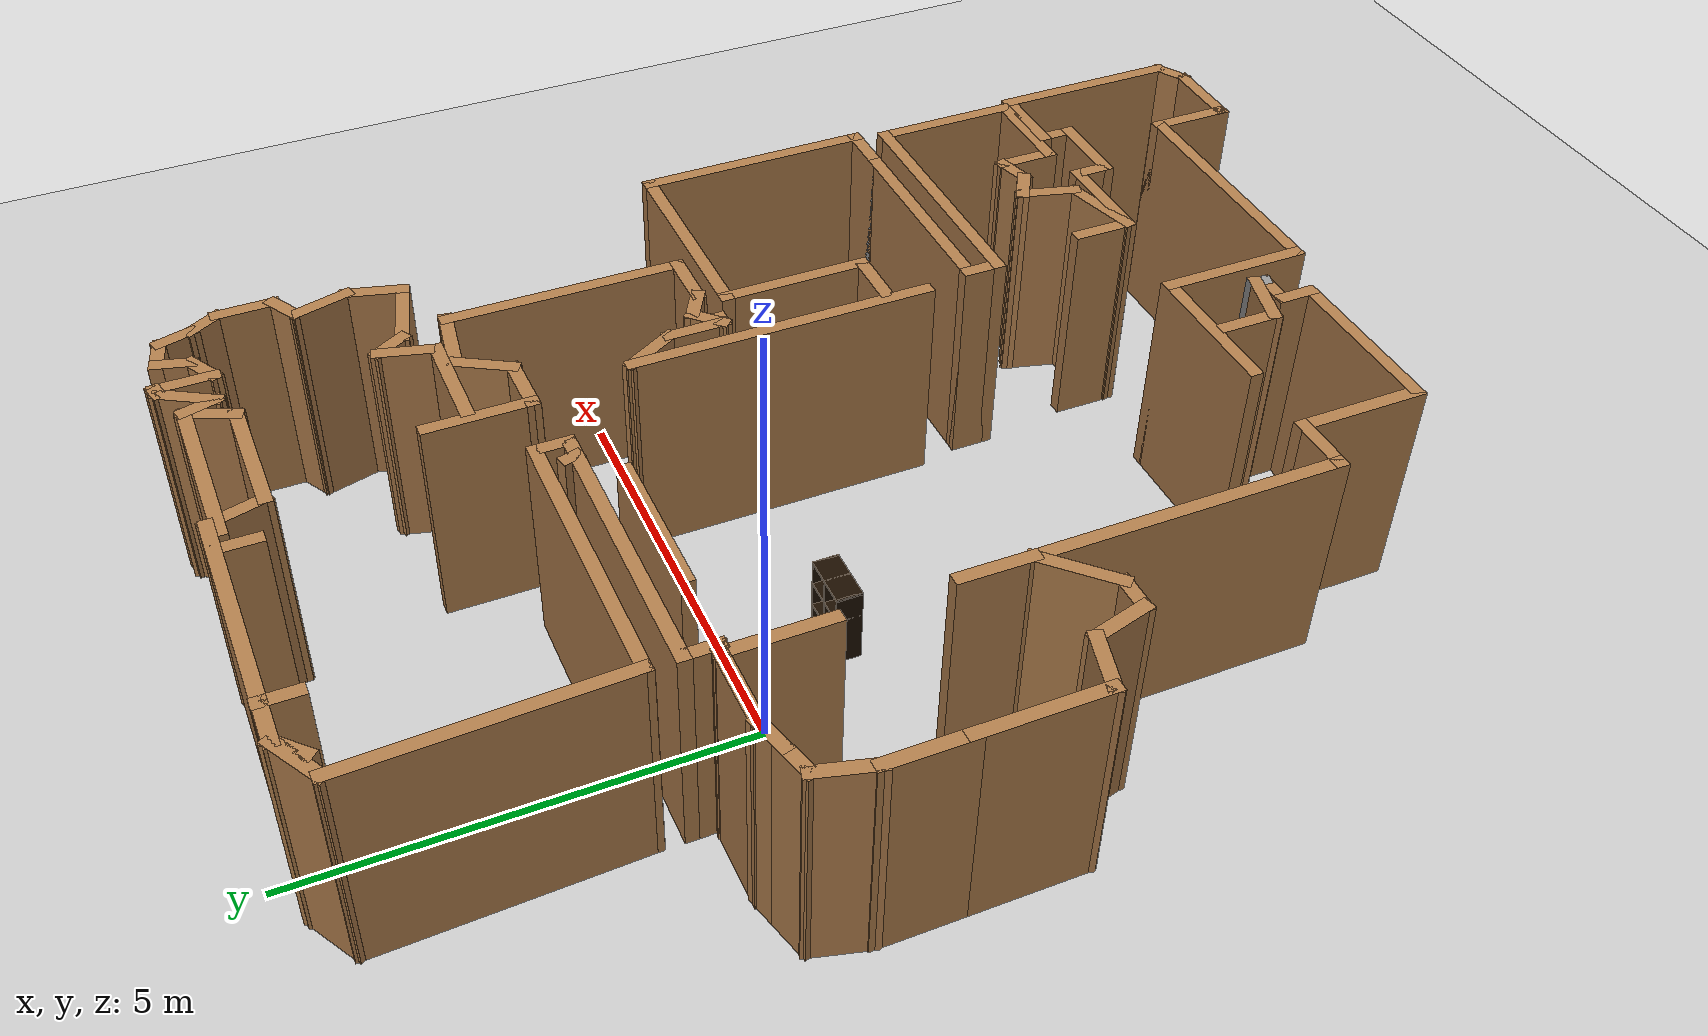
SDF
<sdf version="1.7">
 <world name="default">
  <light name="sun" type="directional">
   <pose>0 0 10 0 -0 0</pose>
   <diffuse>0.8 0.8 0.8 1</diffuse>
   <specular>0.2 0.2 0.2 1</specular>
   <attenuation>
    <range>1000</range>
    <constant>0.9</constant>
    <linear>0.01</linear>
    <quadratic>0.001</quadratic>
   </attenuation>
   <direction>-0.5 0.1 -0.9</direction>
   <spot><inner_angle>0</inner_angle><outer_angle>0</outer_angle><falloff>0</falloff></spot>
  </light>
  <model name="ground_plane">
   <static>1</static>
   <link name="link">
    <collision name="collision">
     <geometry><plane><normal>0 0 1</normal><size>100 100</size></plane></geometry>
     <surface>
      <contact><collide_bitmask>65535</collide_bitmask></contact>
      <friction><ode><mu>100</mu><mu2>50</mu2></ode></friction>
     </surface>
    </collision>
    <visual name="visual">
     <cast_shadows>0</cast_shadows>
     <geometry><plane><normal>0 0 1</normal><size>100 100</size></plane></geometry>
     <material>
      <script><uri>file://media/materials/scripts/gazebo.material</uri><name>Gazebo/Grey</name></script>
     </material>
    </visual>
   </link>
  </model>
  <gravity>0 0 -9.8</gravity>
  <magnetic_field>6e-06 2.3e-05 -4.2e-05</magnetic_field>
  <atmosphere type="adiabatic"/>
  <physics name="default_physics" default="0" type="ode">
   <max_step_size>0.001</max_step_size>
   <real_time_factor>1</real_time_factor>
   <real_time_update_rate>1000</real_time_update_rate>
  </physics>
  <scene><ambient>0.4 0.4 0.4 1</ambient><background>0.7 0.7 0.7 1</background><shadows>1</shadows></scene>
  <audio><device>default</device></audio>
  <spherical_coordinates>
   <surface_model>EARTH_WGS84</surface_model>
   <latitude_deg>0</latitude_deg>
   <longitude_deg>0</longitude_deg>
   <elevation>0</elevation>
   <heading_deg>0</heading_deg>
  </spherical_coordinates>
  <model name="map_9">
   <pose>1.74665 -1.66972 0 0 -0 0</pose>
   <link name="Wall_0">
    <collision name="Wall_0_Collision">
     <geometry><box><size>3 0.15 2.5</size></box></geometry>
     <pose>0 0 1.25 0 -0 0</pose>
    </collision>
    <visual name="Wall_0_Visual">
     <pose>0 0 1.25 0 -0 0</pose>
     <geometry><box><size>3 0.15 2.5</size></box></geometry>
     <material>
      <script><uri>file://media/materials/scripts/gazebo.material</uri><name>Gazebo/Wood</name></script>
      <ambient>1 1 1 1</ambient>
     </material>
     <meta><layer>0</layer></meta>
    </visual>
    <pose>-0.783393 6.3177 0 0 -0 3.14159</pose>
   </link>
   <link name="Wall_1">
    <collision name="Wall_1_Collision">
     <geometry><box><size>0.5 0.15 2.5</size></box></geometry>
     <pose>0 0 1.25 0 -0 0</pose>
    </collision>
    <visual name="Wall_1_Visual">
     <pose>0 0 1.25 0 -0 0</pose>
     <geometry><box><size>0.5 0.15 2.5</size></box></geometry>
     <material>
      <script><uri>file://media/materials/scripts/gazebo.material</uri><name>Gazebo/Wood</name></script>
      <ambient>1 1 1 1</ambient>
     </material>
     <meta><layer>0</layer></meta>
    </visual>
    <pose>-2.33214 6.19396 0 0 -0 -2.35619</pose>
   </link>
   <link name="Wall_10">
    <collision name="Wall_10_Collision">
     <geometry><box><size>3.00225 0.15 2.5</size></box></geometry>
     <pose>0 0 1.25 0 -0 0</pose>
    </collision>
    <visual name="Wall_10_Visual">
     <pose>0 0 1.25 0 -0 0</pose>
     <geometry><box><size>3.00225 0.15 2.5</size></box></geometry>
     <material>
      <script><uri>file://media/materials/scripts/gazebo.material</uri><name>Gazebo/Wood</name></script>
      <ambient>1 1 1 1</ambient>
     </material>
     <meta><layer>0</layer></meta>
    </visual>
    <pose>-2.67944 4.5924 0 0 -0 -1.53674</pose>
   </link>
   <link name="Wall_100">
    <collision name="Wall_100_Collision">
     <geometry><box><size>2.75093 0.15 2.5</size></box></geometry>
     <pose>0 0 1.25 0 -0 0</pose>
    </collision>
    <visual name="Wall_100_Visual">
     <pose>0 0 1.25 0 -0 0</pose>
     <geometry><box><size>2.75093 0.15 2.5</size></box></geometry>
     <material>
      <script><uri>file://media/materials/scripts/gazebo.material</uri><name>Gazebo/Wood</name></script>
      <ambient>1 1 1 1</ambient>
     </material>
     <meta><layer>0</layer></meta>
    </visual>
    <pose>2.82487 2.0909 0 0 -0 1.5619</pose>
   </link>
   <link name="Wall_101">
    <collision name="Wall_101_Collision">
     <geometry><box><size>0.893137 0.15 2.5</size></box></geometry>
     <pose>0 0 1.25 0 -0 0</pose>
    </collision>
    <visual name="Wall_101_Visual">
     <pose>0 0 1.25 0 -0 0</pose>
     <geometry><box><size>0.893137 0.15 2.5</size></box></geometry>
     <material>
      <script><uri>file://media/materials/scripts/gazebo.material</uri><name>Gazebo/Wood</name></script>
      <ambient>1 1 1 1</ambient>
     </material>
     <meta><layer>0</layer></meta>
    </visual>
    <pose>2.49186 3.44439 0 0 -0 2.99715</pose>
   </link>
   <link name="Wall_102">
    <collision name="Wall_102_Collision">
     <geometry><box><size>0.75 0.15 2.5</size></box></geometry>
     <pose>0 0 1.25 0 -0 0</pose>
    </collision>
    <visual name="Wall_102_Visual">
     <pose>0 0 1.25 0 -0 0</pose>
     <geometry><box><size>0.75 0.15 2.5</size></box></geometry>
     <material>
      <script><uri>file://media/materials/scripts/gazebo.material</uri><name>Gazebo/Wood</name></script>
      <ambient>1 1 1 1</ambient>
     </material>
     <meta><layer>0</layer></meta>
    </visual>
    <pose>1.95103 3.23807 0 0 -0 -2.0944</pose>
   </link>
   <link name="Wall_103">
    <collision name="Wall_103_Collision">
     <geometry><box><size>0.762107 0.15 2.5</size></box></geometry>
     <pose>0 0 1.25 0 -0 0</pose>
    </collision>
    <visual name="Wall_103_Visual">
     <pose>0 0 1.25 0 -0 0</pose>
     <geometry><box><size>0.762107 0.15 2.5</size></box></geometry>
     <material>
      <script><uri>file://media/materials/scripts/gazebo.material</uri><name>Gazebo/Wood</name></script>
      <ambient>1 1 1 1</ambient>
     </material>
     <meta><layer>0</layer></meta>
    </visual>
    <pose>1.49503 2.97245 0 0 -0 -3.12261</pose>
   </link>
   <link name="Wall_106">
    <collision name="Wall_106_Collision">
     <geometry><box><size>1.25 0.15 2.5</size></box></geometry>
     <pose>0 0 1.25 0 -0 0</pose>
    </collision>
    <visual name="Wall_106_Visual">
     <pose>0 0 1.25 0 -0 0</pose>
     <geometry><box><size>1.25 0.15 2.5</size></box></geometry>
     <material>
      <script><uri>file://media/materials/scripts/gazebo.material</uri><name>Gazebo/Wood</name></script>
      <ambient>1 1 1 1</ambient>
     </material>
     <meta><layer>0</layer></meta>
    </visual>
    <pose>1.18904 3.51664 0 0 -0 1.5708</pose>
   </link>
   <link name="Wall_108">
    <collision name="Wall_108_Collision">
     <geometry><box><size>1.25 0.15 2.5</size></box></geometry>
     <pose>0 0 1.25 0 -0 0</pose>
    </collision>
    <visual name="Wall_108_Visual">
     <pose>0 0 1.25 0 -0 0</pose>
     <geometry><box><size>1.25 0.15 2.5</size></box></geometry>
     <material>
      <script><uri>file://media/materials/scripts/gazebo.material</uri><name>Gazebo/Wood</name></script>
      <ambient>1 1 1 1</ambient>
     </material>
     <meta><layer>0</layer></meta>
    </visual>
    <pose>1.84331 3.61909 0 0 -0 0</pose>
   </link>
   <link name="Wall_109">
    <collision name="Wall_109_Collision">
     <geometry><box><size>0.75 0.15 2.5</size></box></geometry>
     <pose>0 0 1.25 0 -0 0</pose>
    </collision>
    <visual name="Wall_109_Visual">
     <pose>0 0 1.25 0 -0 0</pose>
     <geometry><box><size>0.75 0.15 2.5</size></box></geometry>
     <material>
      <script><uri>file://media/materials/scripts/gazebo.material</uri><name>Gazebo/Wood</name></script>
      <ambient>1 1 1 1</ambient>
     </material>
     <meta><layer>0</layer></meta>
    </visual>
    <pose>2.47096 3.90887 0 0 -0 1.309</pose>
   </link>
   <link name="Wall_110">
    <collision name="Wall_110_Collision">
     <geometry><box><size>0.5 0.15 2.5</size></box></geometry>
     <pose>0 0 1.25 0 -0 0</pose>
    </collision>
    <visual name="Wall_110_Visual">
     <pose>0 0 1.25 0 -0 0</pose>
     <geometry><box><size>0.5 0.15 2.5</size></box></geometry>
     <material>
      <script><uri>file://media/materials/scripts/gazebo.material</uri><name>Gazebo/Wood</name></script>
      <ambient>1 1 1 1</ambient>
     </material>
     <meta><layer>0</layer></meta>
    </visual>
    <pose>2.6361 4.04709 0 0 -0 -1.0472</pose>
   </link>
   <link name="Wall_111">
    <collision name="Wall_111_Collision">
     <geometry><box><size>1 0.15 2.5</size></box></geometry>
     <pose>0 0 1.25 0 -0 0</pose>
    </collision>
    <visual name="Wall_111_Visual">
     <pose>0 0 1.25 0 -0 0</pose>
     <geometry><box><size>1 0.15 2.5</size></box></geometry>
     <material>
      <script><uri>file://media/materials/scripts/gazebo.material</uri><name>Gazebo/Wood</name></script>
      <ambient>1 1 1 1</ambient>
     </material>
     <meta><layer>0</layer></meta>
    </visual>
    <pose>3.13412 3.78554 0 0 -0 -0.261799</pose>
   </link>
   <link name="Wall_112">
    <collision name="Wall_112_Collision">
     <geometry><box><size>0.75 0.15 2.5</size></box></geometry>
     <pose>0 0 1.25 0 -0 0</pose>
    </collision>
    <visual name="Wall_112_Visual">
     <pose>0 0 1.25 0 -0 0</pose>
     <geometry><box><size>0.75 0.15 2.5</size></box></geometry>
     <material>
      <script><uri>file://media/materials/scripts/gazebo.material</uri><name>Gazebo/Wood</name></script>
      <ambient>1 1 1 1</ambient>
     </material>
     <meta><layer>0</layer></meta>
    </visual>
    <pose>3.62229 3.96532 0 0 -0 1.309</pose>
   </link>
   <link name="Wall_113">
    <collision name="Wall_113_Collision">
     <geometry><box><size>0.75 0.15 2.5</size></box></geometry>
     <pose>0 0 1.25 0 -0 0</pose>
    </collision>
    <visual name="Wall_113_Visual">
     <pose>0 0 1.25 0 -0 0</pose>
     <geometry><box><size>0.75 0.15 2.5</size></box></geometry>
     <material>
      <script><uri>file://media/materials/scripts/gazebo.material</uri><name>Gazebo/Wood</name></script>
      <ambient>1 1 1 1</ambient>
     </material>
     <meta><layer>0</layer></meta>
    </visual>
    <pose>3.62229 4.54487 0 0 -0 1.8326</pose>
   </link>
   <link name="Wall_114">
    <collision name="Wall_114_Collision">
     <geometry><box><size>0.5 0.15 2.5</size></box></geometry>
     <pose>0 0 1.25 0 -0 0</pose>
    </collision>
    <visual name="Wall_114_Visual">
     <pose>0 0 1.25 0 -0 0</pose>
     <geometry><box><size>0.5 0.15 2.5</size></box></geometry>
     <material>
      <script><uri>file://media/materials/scripts/gazebo.material</uri><name>Gazebo/Wood</name></script>
      <ambient>1 1 1 1</ambient>
     </material>
     <meta><layer>0</layer></meta>
    </visual>
    <pose>3.6962 4.92215 0 0 -0 0.523599</pose>
   </link>
   <link name="Wall_115">
    <collision name="Wall_115_Collision">
     <geometry><box><size>0.75 0.15 2.5</size></box></geometry>
     <pose>0 0 1.25 0 -0 0</pose>
    </collision>
    <visual name="Wall_115_Visual">
     <pose>0 0 1.25 0 -0 0</pose>
     <geometry><box><size>0.75 0.15 2.5</size></box></geometry>
     <material>
      <script><uri>file://media/materials/scripts/gazebo.material</uri><name>Gazebo/Wood</name></script>
      <ambient>1 1 1 1</ambient>
     </material>
     <meta><layer>0</layer></meta>
    </visual>
    <pose>3.84775 5.30965 0 0 -0 1.5708</pose>
   </link>
   <link name="Wall_116">
    <collision name="Wall_116_Collision">
     <geometry><box><size>0.5 0.15 2.5</size></box></geometry>
     <pose>0 0 1.25 0 -0 0</pose>
    </collision>
    <visual name="Wall_116_Visual">
     <pose>0 0 1.25 0 -0 0</pose>
     <geometry><box><size>0.5 0.15 2.5</size></box></geometry>
     <material>
      <script><uri>file://media/materials/scripts/gazebo.material</uri><name>Gazebo/Wood</name></script>
      <ambient>1 1 1 1</ambient>
     </material>
     <meta><layer>0</layer></meta>
    </visual>
    <pose>3.76025 5.76121 0 0 -0 2.0944</pose>
   </link>
   <link name="Wall_117">
    <collision name="Wall_117_Collision">
     <geometry><box><size>0.5 0.15 2.5</size></box></geometry>
     <pose>0 0 1.25 0 -0 0</pose>
    </collision>
    <visual name="Wall_117_Visual">
     <pose>0 0 1.25 0 -0 0</pose>
     <geometry><box><size>0.5 0.15 2.5</size></box></geometry>
     <material>
      <script><uri>file://media/materials/scripts/gazebo.material</uri><name>Gazebo/Wood</name></script>
      <ambient>1 1 1 1</ambient>
     </material>
     <meta><layer>0</layer></meta>
    </visual>
    <pose>3.62746 6.0818 0 0 -0 1.8326</pose>
   </link>
   <link name="Wall_118">
    <collision name="Wall_118_Collision">
     <geometry><box><size>0.5 0.15 2.5</size></box></geometry>
     <pose>0 0 1.25 0 -0 0</pose>
    </collision>
    <visual name="Wall_118_Visual">
     <pose>0 0 1.25 0 -0 0</pose>
     <geometry><box><size>0.5 0.15 2.5</size></box></geometry>
     <material>
      <script><uri>file://media/materials/scripts/gazebo.material</uri><name>Gazebo/Wood</name></script>
      <ambient>1 1 1 1</ambient>
     </material>
     <meta><layer>0</layer></meta>
    </visual>
    <pose>3.41313 6.29613 0 0 -0 2.87979</pose>
   </link>
   <link name="Wall_119">
    <collision name="Wall_119_Collision">
     <geometry><box><size>0.5 0.15 2.5</size></box></geometry>
     <pose>0 0 1.25 0 -0 0</pose>
    </collision>
    <visual name="Wall_119_Visual">
     <pose>0 0 1.25 0 -0 0</pose>
     <geometry><box><size>0.5 0.15 2.5</size></box></geometry>
     <material>
      <script><uri>file://media/materials/scripts/gazebo.material</uri><name>Gazebo/Wood</name></script>
      <ambient>1 1 1 1</ambient>
     </material>
     <meta><layer>0</layer></meta>
    </visual>
    <pose>3.1988 6.17238 0 0 -0 -1.8326</pose>
   </link>
   <link name="Wall_120">
    <collision name="Wall_120_Collision">
     <geometry><box><size>0.5 0.15 2.5</size></box></geometry>
     <pose>0 0 1.25 0 -0 0</pose>
    </collision>
    <visual name="Wall_120_Visual">
     <pose>0 0 1.25 0 -0 0</pose>
     <geometry><box><size>0.5 0.15 2.5</size></box></geometry>
     <material>
      <script><uri>file://media/materials/scripts/gazebo.material</uri><name>Gazebo/Wood</name></script>
      <ambient>1 1 1 1</ambient>
     </material>
     <meta><layer>0</layer></meta>
    </visual>
    <pose>3.00195 5.91585 0 0 -0 -2.61799</pose>
   </link>
   <link name="Wall_121">
    <collision name="Wall_121_Collision">
     <geometry><box><size>0.75 0.15 2.5</size></box></geometry>
     <pose>0 0 1.25 0 -0 0</pose>
    </collision>
    <visual name="Wall_121_Visual">
     <pose>0 0 1.25 0 -0 0</pose>
     <geometry><box><size>0.75 0.15 2.5</size></box></geometry>
     <material>
      <script><uri>file://media/materials/scripts/gazebo.material</uri><name>Gazebo/Wood</name></script>
      <ambient>1 1 1 1</ambient>
     </material>
     <meta><layer>0</layer></meta>
    </visual>
    <pose>2.85039 6.12835 0 0 -0 1.5708</pose>
   </link>
   <link name="Wall_122">
    <collision name="Wall_122_Collision">
     <geometry><box><size>0.25 0.15 2.5</size></box></geometry>
     <pose>0 0 1.25 0 -0 0</pose>
    </collision>
    <visual name="Wall_122_Visual">
     <pose>0 0 1.25 0 -0 0</pose>
     <geometry><box><size>0.25 0.15 2.5</size></box></geometry>
     <material>
      <script><uri>file://media/materials/scripts/gazebo.material</uri><name>Gazebo/Wood</name></script>
      <ambient>1 1 1 1</ambient>
     </material>
     <meta><layer>0</layer></meta>
    </visual>
    <pose>2.8021 6.4154 0 0 -0 -2.87979</pose>
   </link>
   <link name="Wall_123">
    <collision name="Wall_123_Collision">
     <geometry><box><size>0.75 0.15 2.5</size></box></geometry>
     <pose>0 0 1.25 0 -0 0</pose>
    </collision>
    <visual name="Wall_123_Visual">
     <pose>0 0 1.25 0 -0 0</pose>
     <geometry><box><size>0.75 0.15 2.5</size></box></geometry>
     <material>
      <script><uri>file://media/materials/scripts/gazebo.material</uri><name>Gazebo/Wood</name></script>
      <ambient>1 1 1 1</ambient>
     </material>
     <meta><layer>0</layer></meta>
    </visual>
    <pose>2.6038 6.14266 0 0 -0 -2.0944</pose>
   </link>
   <link name="Wall_124">
    <collision name="Wall_124_Collision">
     <geometry><box><size>0.5 0.15 2.5</size></box></geometry>
     <pose>0 0 1.25 0 -0 0</pose>
    </collision>
    <visual name="Wall_124_Visual">
     <pose>0 0 1.25 0 -0 0</pose>
     <geometry><box><size>0.5 0.15 2.5</size></box></geometry>
     <material>
      <script><uri>file://media/materials/scripts/gazebo.material</uri><name>Gazebo/Wood</name></script>
      <ambient>1 1 1 1</ambient>
     </material>
     <meta><layer>0</layer></meta>
    </visual>
    <pose>2.40851 6.05189 0 0 -0 1.8326</pose>
   </link>
   <link name="Wall_125">
    <collision name="Wall_125_Collision">
     <geometry><box><size>2 0.15 2.5</size></box></geometry>
     <pose>0 0 1.25 0 -0 0</pose>
    </collision>
    <visual name="Wall_125_Visual">
     <pose>0 0 1.25 0 -0 0</pose>
     <geometry><box><size>2 0.15 2.5</size></box></geometry>
     <material>
      <script><uri>file://media/materials/scripts/gazebo.material</uri><name>Gazebo/Wood</name></script>
      <ambient>1 1 1 1</ambient>
     </material>
     <meta><layer>0</layer></meta>
    </visual>
    <pose>1.43822 6.22092 0 0 -0 3.14159</pose>
   </link>
   <link name="Wall_128">
    <collision name="Wall_128_Collision">
     <geometry><box><size>0.75 0.15 2.5</size></box></geometry>
     <pose>0 0 1.25 0 -0 0</pose>
    </collision>
    <visual name="Wall_128_Visual">
     <pose>0 0 1.25 0 -0 0</pose>
     <geometry><box><size>0.75 0.15 2.5</size></box></geometry>
     <material>
      <script><uri>file://media/materials/scripts/gazebo.material</uri><name>Gazebo/Wood</name></script>
      <ambient>1 1 1 1</ambient>
     </material>
     <meta><layer>0</layer></meta>
    </visual>
    <pose>0.719253 6.02792 0 0 -0 -1.309</pose>
   </link>
   <link name="Wall_129">
    <collision name="Wall_129_Collision">
     <geometry><box><size>1.5 0.15 2.5</size></box></geometry>
     <pose>0 0 1.25 0 -0 0</pose>
    </collision>
    <visual name="Wall_129_Visual">
     <pose>0 0 1.25 0 -0 0</pose>
     <geometry><box><size>1.5 0.15 2.5</size></box></geometry>
     <material>
      <script><uri>file://media/materials/scripts/gazebo.material</uri><name>Gazebo/Wood</name></script>
      <ambient>1 1 1 1</ambient>
     </material>
     <meta><layer>0</layer></meta>
    </visual>
    <pose>1.4719 5.73815 0 0 -0 0</pose>
   </link>
   <link name="Wall_130">
    <collision name="Wall_130_Collision">
     <geometry><box><size>0.679025 0.15 2.5</size></box></geometry>
     <pose>0 0 1.25 0 -0 0</pose>
    </collision>
    <visual name="Wall_130_Visual">
     <pose>0 0 1.25 0 -0 0</pose>
     <geometry><box><size>0.679025 0.15 2.5</size></box></geometry>
     <material>
      <script><uri>file://media/materials/scripts/gazebo.material</uri><name>Gazebo/Wood</name></script>
      <ambient>1 1 1 1</ambient>
     </material>
     <meta><layer>0</layer></meta>
    </visual>
    <pose>2.25506 5.97953 0 0 -0 1.14955</pose>
   </link>
   <link name="Wall_132">
    <collision name="Wall_132_Collision">
     <geometry><box><size>0.5 0.15 2.5</size></box></geometry>
     <pose>0 0 1.25 0 -0 0</pose>
    </collision>
    <visual name="Wall_132_Visual">
     <pose>0 0 1.25 0 -0 0</pose>
     <geometry><box><size>0.5 0.15 2.5</size></box></geometry>
     <material>
      <script><uri>file://media/materials/scripts/gazebo.material</uri><name>Gazebo/Wood</name></script>
      <ambient>1 1 1 1</ambient>
     </material>
     <meta><layer>0</layer></meta>
    </visual>
    <pose>-1.73728 6.15158 0 0 -0 -1.5708</pose>
   </link>
   <link name="Wall_134">
    <collision name="Wall_134_Collision">
     <geometry><box><size>0.5 0.15 2.5</size></box></geometry>
     <pose>0 0 1.25 0 -0 0</pose>
    </collision>
    <visual name="Wall_134_Visual">
     <pose>0 0 1.25 0 -0 0</pose>
     <geometry><box><size>0.5 0.15 2.5</size></box></geometry>
     <material>
      <script><uri>file://media/materials/scripts/gazebo.material</uri><name>Gazebo/Wood</name></script>
      <ambient>1 1 1 1</ambient>
     </material>
     <meta><layer>0</layer></meta>
    </visual>
    <pose>0.281673 6.0904 0 0 -0 -1.5708</pose>
   </link>
   <link name="Wall_136">
    <collision name="Wall_136_Collision">
     <geometry><box><size>1.75 0.15 2.5</size></box></geometry>
     <pose>0 0 1.25 0 -0 0</pose>
    </collision>
    <visual name="Wall_136_Visual">
     <pose>0 0 1.25 0 -0 0</pose>
     <geometry><box><size>1.75 0.15 2.5</size></box></geometry>
     <material>
      <script><uri>file://media/materials/scripts/gazebo.material</uri><name>Gazebo/Wood</name></script>
      <ambient>1 1 1 1</ambient>
     </material>
     <meta><layer>0</layer></meta>
    </visual>
    <pose>-0.937282 2.44162 0 0 -0 0</pose>
   </link>
   <link name="Wall_138">
    <collision name="Wall_138_Collision">
     <geometry><box><size>1.25 0.15 2.5</size></box></geometry>
     <pose>0 0 1.25 0 -0 0</pose>
    </collision>
    <visual name="Wall_138_Visual">
     <pose>0 0 1.25 0 -0 0</pose>
     <geometry><box><size>1.25 0.15 2.5</size></box></geometry>
     <material>
      <script><uri>file://media/materials/scripts/gazebo.material</uri><name>Gazebo/Wood</name></script>
      <ambient>1 1 1 1</ambient>
     </material>
     <meta><layer>0</layer></meta>
    </visual>
    <pose>-2.72747 1.94299 0 0 -0 -1.5708</pose>
   </link>
   <link name="Wall_14">
    <collision name="Wall_14_Collision">
     <geometry><box><size>0.25 0.15 2.5</size></box></geometry>
     <pose>0 0 1.25 0 -0 0</pose>
    </collision>
    <visual name="Wall_14_Visual">
     <pose>0 0 1.25 0 -0 0</pose>
     <geometry><box><size>0.25 0.15 2.5</size></box></geometry>
     <material>
      <script><uri>file://media/materials/scripts/gazebo.material</uri><name>Gazebo/Wood</name></script>
      <ambient>1 1 1 1</ambient>
     </material>
     <meta><layer>0</layer></meta>
    </visual>
    <pose>0.229548 2.87132 0 0 -0 -1.309</pose>
   </link>
   <link name="Wall_140">
    <collision name="Wall_140_Collision">
     <geometry><box><size>0.898938 0.15 2.5</size></box></geometry>
     <pose>0 0 1.25 0 -0 0</pose>
    </collision>
    <visual name="Wall_140_Visual">
     <pose>0 0 1.25 0 -0 0</pose>
     <geometry><box><size>0.898938 0.15 2.5</size></box></geometry>
     <material>
      <script><uri>file://media/materials/scripts/gazebo.material</uri><name>Gazebo/Wood</name></script>
      <ambient>1 1 1 1</ambient>
     </material>
     <meta><layer>0</layer></meta>
    </visual>
    <pose>-2.7196 -0.227096 0 0 -0 -1.57995</pose>
   </link>
   <link name="Wall_16">
    <collision name="Wall_16_Collision">
     <geometry><box><size>3.25 0.15 2.5</size></box></geometry>
     <pose>0 0 1.25 0 -0 0</pose>
    </collision>
    <visual name="Wall_16_Visual">
     <pose>0 0 1.25 0 -0 0</pose>
     <geometry><box><size>3.25 0.15 2.5</size></box></geometry>
     <material>
      <script><uri>file://media/materials/scripts/gazebo.material</uri><name>Gazebo/Wood</name></script>
      <ambient>1 1 1 1</ambient>
     </material>
     <meta><layer>0</layer></meta>
    </visual>
    <pose>-1.08088 3.1671 0 0 -0 0</pose>
   </link>
   <link name="Wall_17">
    <collision name="Wall_17_Collision">
     <geometry><box><size>0.5 0.15 2.5</size></box></geometry>
     <pose>0 0 1.25 0 -0 0</pose>
    </collision>
    <visual name="Wall_17_Visual">
     <pose>0 0 1.25 0 -0 0</pose>
     <geometry><box><size>0.5 0.15 2.5</size></box></geometry>
     <material>
      <script><uri>file://media/materials/scripts/gazebo.material</uri><name>Gazebo/Wood</name></script>
      <ambient>1 1 1 1</ambient>
     </material>
     <meta><layer>0</layer></meta>
    </visual>
    <pose>0.46912 2.9921 0 0 -0 -1.5708</pose>
   </link>
   <link name="Wall_18">
    <collision name="Wall_18_Collision">
     <geometry><box><size>3.25 0.15 2.5</size></box></geometry>
     <pose>0 0 1.25 0 -0 0</pose>
    </collision>
    <visual name="Wall_18_Visual">
     <pose>0 0 1.25 0 -0 0</pose>
     <geometry><box><size>3.25 0.15 2.5</size></box></geometry>
     <material>
      <script><uri>file://media/materials/scripts/gazebo.material</uri><name>Gazebo/Wood</name></script>
      <ambient>1 1 1 1</ambient>
     </material>
     <meta><layer>0</layer></meta>
    </visual>
    <pose>-1.08088 2.8171 0 0 -0 3.14159</pose>
   </link>
   <link name="Wall_19">
    <collision name="Wall_19_Collision">
     <geometry><box><size>0.5 0.15 2.5</size></box></geometry>
     <pose>0 0 1.25 0 -0 0</pose>
    </collision>
    <visual name="Wall_19_Visual">
     <pose>0 0 1.25 0 -0 0</pose>
     <geometry><box><size>0.5 0.15 2.5</size></box></geometry>
     <material>
      <script><uri>file://media/materials/scripts/gazebo.material</uri><name>Gazebo/Wood</name></script>
      <ambient>1 1 1 1</ambient>
     </material>
     <meta><layer>0</layer></meta>
    </visual>
    <pose>-2.63088 2.6421 0 0 -0 -1.5708</pose>
   </link>
   <link name="Wall_20">
    <collision name="Wall_20_Collision">
     <geometry><box><size>0.25 0.15 2.5</size></box></geometry>
     <pose>0 0 1.25 0 -0 0</pose>
    </collision>
    <visual name="Wall_20_Visual">
     <pose>0 0 1.25 0 -0 0</pose>
     <geometry><box><size>0.25 0.15 2.5</size></box></geometry>
     <material>
      <script><uri>file://media/materials/scripts/gazebo.material</uri><name>Gazebo/Wood</name></script>
      <ambient>1 1 1 1</ambient>
     </material>
     <meta><layer>0</layer></meta>
    </visual>
    <pose>-2.67918 2.48005 0 0 -0 2.87979</pose>
   </link>
   <link name="Wall_21">
    <collision name="Wall_21_Collision">
     <geometry><box><size>1 0.15 2.5</size></box></geometry>
     <pose>0 0 1.25 0 -0 0</pose>
    </collision>
    <visual name="Wall_21_Visual">
     <pose>0 0 1.25 0 -0 0</pose>
     <geometry><box><size>1 0.15 2.5</size></box></geometry>
     <material>
      <script><uri>file://media/materials/scripts/gazebo.material</uri><name>Gazebo/Wood</name></script>
      <ambient>1 1 1 1</ambient>
     </material>
     <meta><layer>0</layer></meta>
    </visual>
    <pose>-3.15247 2.49299 0 0 -0 3.14159</pose>
   </link>
   <link name="Wall_22">
    <collision name="Wall_22_Collision">
     <geometry><box><size>0.5 0.15 2.5</size></box></geometry>
     <pose>0 0 1.25 0 -0 0</pose>
    </collision>
    <visual name="Wall_22_Visual">
     <pose>0 0 1.25 0 -0 0</pose>
     <geometry><box><size>0.5 0.15 2.5</size></box></geometry>
     <material>
      <script><uri>file://media/materials/scripts/gazebo.material</uri><name>Gazebo/Wood</name></script>
      <ambient>1 1 1 1</ambient>
     </material>
     <meta><layer>0</layer></meta>
    </visual>
    <pose>-3.74651 2.44769 0 0 -0 -2.87979</pose>
   </link>
   <link name="Wall_23">
    <collision name="Wall_23_Collision">
     <geometry><box><size>0.5 0.15 2.5</size></box></geometry>
     <pose>0 0 1.25 0 -0 0</pose>
    </collision>
    <visual name="Wall_23_Visual">
     <pose>0 0 1.25 0 -0 0</pose>
     <geometry><box><size>0.5 0.15 2.5</size></box></geometry>
     <material>
      <script><uri>file://media/materials/scripts/gazebo.material</uri><name>Gazebo/Wood</name></script>
      <ambient>1 1 1 1</ambient>
     </material>
     <meta><layer>0</layer></meta>
    </visual>
    <pose>-4.08458 2.35711 0 0 -0 -2.87979</pose>
   </link>
   <link name="Wall_24">
    <collision name="Wall_24_Collision">
     <geometry><box><size>0.75 0.15 2.5</size></box></geometry>
     <pose>0 0 1.25 0 -0 0</pose>
    </collision>
    <visual name="Wall_24_Visual">
     <pose>0 0 1.25 0 -0 0</pose>
     <geometry><box><size>0.75 0.15 2.5</size></box></geometry>
     <material>
      <script><uri>file://media/materials/scripts/gazebo.material</uri><name>Gazebo/Wood</name></script>
      <ambient>1 1 1 1</ambient>
     </material>
     <meta><layer>0</layer></meta>
    </visual>
    <pose>-4.33127 2.02203 0 0 -0 -1.8326</pose>
   </link>
   <link name="Wall_25">
    <collision name="Wall_25_Collision">
     <geometry><box><size>1 0.15 2.5</size></box></geometry>
     <pose>0 0 1.25 0 -0 0</pose>
    </collision>
    <visual name="Wall_25_Visual">
     <pose>0 0 1.25 0 -0 0</pose>
     <geometry><box><size>1 0.15 2.5</size></box></geometry>
     <material>
      <script><uri>file://media/materials/scripts/gazebo.material</uri><name>Gazebo/Wood</name></script>
      <ambient>1 1 1 1</ambient>
     </material>
     <meta><layer>0</layer></meta>
    </visual>
    <pose>-4.40891 1.30726 0 0 -0 -1.5708</pose>
   </link>
   <link name="Wall_26">
    <collision name="Wall_26_Collision">
     <geometry><box><size>1.5 0.15 2.5</size></box></geometry>
     <pose>0 0 1.25 0 -0 0</pose>
    </collision>
    <visual name="Wall_26_Visual">
     <pose>0 0 1.25 0 -0 0</pose>
     <geometry><box><size>1.5 0.15 2.5</size></box></geometry>
     <material>
      <script><uri>file://media/materials/scripts/gazebo.material</uri><name>Gazebo/Wood</name></script>
      <ambient>1 1 1 1</ambient>
     </material>
     <meta><layer>0</layer></meta>
    </visual>
    <pose>-4.40891 0.207257 0 0 -0 -1.5708</pose>
   </link>
   <link name="Wall_27">
    <collision name="Wall_27_Collision">
     <geometry><box><size>0.75 0.15 2.5</size></box></geometry>
     <pose>0 0 1.25 0 -0 0</pose>
    </collision>
    <visual name="Wall_27_Visual">
     <pose>0 0 1.25 0 -0 0</pose>
     <geometry><box><size>0.75 0.15 2.5</size></box></geometry>
     <material>
      <script><uri>file://media/materials/scripts/gazebo.material</uri><name>Gazebo/Wood</name></script>
      <ambient>1 1 1 1</ambient>
     </material>
     <meta><layer>0</layer></meta>
    </visual>
    <pose>-4.11913 -0.545389 0 0 -0 -0.261799</pose>
   </link>
   <link name="Wall_28">
    <collision name="Wall_28_Collision">
     <geometry><box><size>0.75 0.15 2.5</size></box></geometry>
     <pose>0 0 1.25 0 -0 0</pose>
    </collision>
    <visual name="Wall_28_Visual">
     <pose>0 0 1.25 0 -0 0</pose>
     <geometry><box><size>0.75 0.15 2.5</size></box></geometry>
     <material>
      <script><uri>file://media/materials/scripts/gazebo.material</uri><name>Gazebo/Wood</name></script>
      <ambient>1 1 1 1</ambient>
     </material>
     <meta><layer>0</layer></meta>
    </visual>
    <pose>-3.75171 -0.912812 0 0 -0 -1.309</pose>
   </link>
   <link name="Wall_29">
    <collision name="Wall_29_Collision">
     <geometry><box><size>0.5 0.15 2.5</size></box></geometry>
     <pose>0 0 1.25 0 -0 0</pose>
    </collision>
    <visual name="Wall_29_Visual">
     <pose>0 0 1.25 0 -0 0</pose>
     <geometry><box><size>0.5 0.15 2.5</size></box></geometry>
     <material>
      <script><uri>file://media/materials/scripts/gazebo.material</uri><name>Gazebo/Wood</name></script>
      <ambient>1 1 1 1</ambient>
     </material>
     <meta><layer>0</layer></meta>
    </visual>
    <pose>-3.49906 -1.20259 0 0 -0 0</pose>
   </link>
   <link name="Wall_30">
    <collision name="Wall_30_Collision">
     <geometry><box><size>1 0.15 2.5</size></box></geometry>
     <pose>0 0 1.25 0 -0 0</pose>
    </collision>
    <visual name="Wall_30_Visual">
     <pose>0 0 1.25 0 -0 0</pose>
     <geometry><box><size>1 0.15 2.5</size></box></geometry>
     <material>
      <script><uri>file://media/materials/scripts/gazebo.material</uri><name>Gazebo/Wood</name></script>
      <ambient>1 1 1 1</ambient>
     </material>
     <meta><layer>0</layer></meta>
    </visual>
    <pose>-3.02354 -0.902069 0 0 -0 0.785398</pose>
   </link>
   <link name="Wall_31">
    <collision name="Wall_31_Collision">
     <geometry><box><size>3.5 0.15 2.5</size></box></geometry>
     <pose>0 0 1.25 0 -0 0</pose>
    </collision>
    <visual name="Wall_31_Visual">
     <pose>0 0 1.25 0 -0 0</pose>
     <geometry><box><size>3.5 0.15 2.5</size></box></geometry>
     <material>
      <script><uri>file://media/materials/scripts/gazebo.material</uri><name>Gazebo/Wood</name></script>
      <ambient>1 1 1 1</ambient>
     </material>
     <meta><layer>0</layer></meta>
    </visual>
    <pose>-2.72302 -2.27655 0 0 -0 -1.5708</pose>
   </link>
   <link name="Wall_32">
    <collision name="Wall_32_Collision">
     <geometry><box><size>0.75 0.15 2.5</size></box></geometry>
     <pose>0 0 1.25 0 -0 0</pose>
    </collision>
    <visual name="Wall_32_Visual">
     <pose>0 0 1.25 0 -0 0</pose>
     <geometry><box><size>0.75 0.15 2.5</size></box></geometry>
     <material>
      <script><uri>file://media/materials/scripts/gazebo.material</uri><name>Gazebo/Wood</name></script>
      <ambient>1 1 1 1</ambient>
     </material>
     <meta><layer>0</layer></meta>
    </visual>
    <pose>-2.42302 -3.95155 0 0 -0 0</pose>
   </link>
   <link name="Wall_33">
    <collision name="Wall_33_Collision">
     <geometry><box><size>1.5 0.15 2.5</size></box></geometry>
     <pose>0 0 1.25 0 -0 0</pose>
    </collision>
    <visual name="Wall_33_Visual">
     <pose>0 0 1.25 0 -0 0</pose>
     <geometry><box><size>1.5 0.15 2.5</size></box></geometry>
     <material>
      <script><uri>file://media/materials/scripts/gazebo.material</uri><name>Gazebo/Wood</name></script>
      <ambient>1 1 1 1</ambient>
     </material>
     <meta><layer>0</layer></meta>
    </visual>
    <pose>-2.12302 -4.62655 0 0 -0 -1.5708</pose>
   </link>
   <link name="Wall_34">
    <collision name="Wall_34_Collision">
     <geometry><box><size>2 0.15 2.5</size></box></geometry>
     <pose>0 0 1.25 0 -0 0</pose>
    </collision>
    <visual name="Wall_34_Visual">
     <pose>0 0 1.25 0 -0 0</pose>
     <geometry><box><size>2 0.15 2.5</size></box></geometry>
     <material>
      <script><uri>file://media/materials/scripts/gazebo.material</uri><name>Gazebo/Wood</name></script>
      <ambient>1 1 1 1</ambient>
     </material>
     <meta><layer>0</layer></meta>
    </visual>
    <pose>-1.19802 -5.30155 0 0 -0 0</pose>
   </link>
   <link name="Wall_35">
    <collision name="Wall_35_Collision">
     <geometry><box><size>0.5 0.15 2.5</size></box></geometry>
     <pose>0 0 1.25 0 -0 0</pose>
    </collision>
    <visual name="Wall_35_Visual">
     <pose>0 0 1.25 0 -0 0</pose>
     <geometry><box><size>0.5 0.15 2.5</size></box></geometry>
     <material>
      <script><uri>file://media/materials/scripts/gazebo.material</uri><name>Gazebo/Wood</name></script>
      <ambient>1 1 1 1</ambient>
     </material>
     <meta><layer>0</layer></meta>
    </visual>
    <pose>-0.273024 -5.12655 0 0 -0 1.5708</pose>
   </link>
   <link name="Wall_36">
    <collision name="Wall_36_Collision">
     <geometry><box><size>0.5 0.15 2.5</size></box></geometry>
     <pose>0 0 1.25 0 -0 0</pose>
    </collision>
    <visual name="Wall_36_Visual">
     <pose>0 0 1.25 0 -0 0</pose>
     <geometry><box><size>0.5 0.15 2.5</size></box></geometry>
     <material>
      <script><uri>file://media/materials/scripts/gazebo.material</uri><name>Gazebo/Wood</name></script>
      <ambient>1 1 1 1</ambient>
     </material>
     <meta><layer>0</layer></meta>
    </visual>
    <pose>-0.098024 -4.95155 0 0 -0 0</pose>
   </link>
   <link name="Wall_37">
    <collision name="Wall_37_Collision">
     <geometry><box><size>0.25 0.15 2.5</size></box></geometry>
     <pose>0 0 1.25 0 -0 0</pose>
    </collision>
    <visual name="Wall_37_Visual">
     <pose>0 0 1.25 0 -0 0</pose>
     <geometry><box><size>0.25 0.15 2.5</size></box></geometry>
     <material>
      <script><uri>file://media/materials/scripts/gazebo.material</uri><name>Gazebo/Grey</name></script>
      <ambient>1 1 1 1</ambient>
     </material>
     <meta><layer>0</layer></meta>
    </visual>
    <pose>0.089917 -4.90325 0 0 -0 1.309</pose>
   </link>
   <link name="Wall_40">
    <collision name="Wall_40_Collision">
     <geometry><box><size>0.25 0.15 2.5</size></box></geometry>
     <pose>0 0 1.25 0 -0 0</pose>
    </collision>
    <visual name="Wall_40_Visual">
     <pose>0 0 1.25 0 -0 0</pose>
     <geometry><box><size>0.25 0.15 2.5</size></box></geometry>
     <material>
      <script><uri>file://media/materials/scripts/gazebo.material</uri><name>Gazebo/Wood</name></script>
      <ambient>1 1 1 1</ambient>
     </material>
     <meta><layer>0</layer></meta>
    </visual>
    <pose>0.089917 -4.90325 0 0 -0 1.309</pose>
   </link>
   <link name="Wall_41">
    <collision name="Wall_41_Collision">
     <geometry><box><size>0.75 0.15 2.5</size></box></geometry>
     <pose>0 0 1.25 0 -0 0</pose>
    </collision>
    <visual name="Wall_41_Visual">
     <pose>0 0 1.25 0 -0 0</pose>
     <geometry><box><size>0.75 0.15 2.5</size></box></geometry>
     <material>
      <script><uri>file://media/materials/scripts/gazebo.material</uri><name>Gazebo/Wood</name></script>
      <ambient>1 1 1 1</ambient>
     </material>
     <meta><layer>0</layer></meta>
    </visual>
    <pose>-0.18692 -4.77731 0 0 -0 2.87979</pose>
   </link>
   <link name="Wall_44">
    <collision name="Wall_44_Collision">
     <geometry><box><size>0.75 0.15 2.5</size></box></geometry>
     <pose>0 0 1.25 0 -0 0</pose>
    </collision>
    <visual name="Wall_44_Visual">
     <pose>0 0 1.25 0 -0 0</pose>
     <geometry><box><size>0.75 0.15 2.5</size></box></geometry>
     <material>
      <script><uri>file://media/materials/scripts/gazebo.material</uri><name>Gazebo/Wood</name></script>
      <ambient>1 1 1 1</ambient>
     </material>
     <meta><layer>0</layer></meta>
    </visual>
    <pose>-0.476698 -4.39966 0 0 -0 1.5708</pose>
   </link>
   <link name="Wall_46">
    <collision name="Wall_46_Collision">
     <geometry><box><size>1.75 0.15 2.5</size></box></geometry>
     <pose>0 0 1.25 0 -0 0</pose>
    </collision>
    <visual name="Wall_46_Visual">
     <pose>0 0 1.25 0 -0 0</pose>
     <geometry><box><size>1.75 0.15 2.5</size></box></geometry>
     <material>
      <script><uri>file://media/materials/scripts/gazebo.material</uri><name>Gazebo/Wood</name></script>
      <ambient>1 1 1 1</ambient>
     </material>
     <meta><layer>0</layer></meta>
    </visual>
    <pose>-0.404793 -3.96775 0 0 -0 0</pose>
   </link>
   <link name="Wall_47">
    <collision name="Wall_47_Collision">
     <geometry><box><size>1.75 0.15 2.5</size></box></geometry>
     <pose>0 0 1.25 0 -0 0</pose>
    </collision>
    <visual name="Wall_47_Visual">
     <pose>0 0 1.25 0 -0 0</pose>
     <geometry><box><size>1.75 0.15 2.5</size></box></geometry>
     <material>
      <script><uri>file://media/materials/scripts/gazebo.material</uri><name>Gazebo/Wood</name></script>
      <ambient>1 1 1 1</ambient>
     </material>
     <meta><layer>0</layer></meta>
    </visual>
    <pose>0.395207 -4.76775 0 0 -0 -1.5708</pose>
   </link>
   <link name="Wall_48">
    <collision name="Wall_48_Collision">
     <geometry><box><size>3 0.15 2.5</size></box></geometry>
     <pose>0 0 1.25 0 -0 0</pose>
    </collision>
    <visual name="Wall_48_Visual">
     <pose>0 0 1.25 0 -0 0</pose>
     <geometry><box><size>3 0.15 2.5</size></box></geometry>
     <material>
      <script><uri>file://media/materials/scripts/gazebo.material</uri><name>Gazebo/Wood</name></script>
      <ambient>1 1 1 1</ambient>
     </material>
     <meta><layer>0</layer></meta>
    </visual>
    <pose>1.82021 -5.56775 0 0 -0 0</pose>
   </link>
   <link name="Wall_49">
    <collision name="Wall_49_Collision">
     <geometry><box><size>1 0.15 2.5</size></box></geometry>
     <pose>0 0 1.25 0 -0 0</pose>
    </collision>
    <visual name="Wall_49_Visual">
     <pose>0 0 1.25 0 -0 0</pose>
     <geometry><box><size>1 0.15 2.5</size></box></geometry>
     <material>
      <script><uri>file://media/materials/scripts/gazebo.material</uri><name>Gazebo/Wood</name></script>
      <ambient>1 1 1 1</ambient>
     </material>
     <meta><layer>0</layer></meta>
    </visual>
    <pose>3.24521 -5.99275 0 0 -0 -1.5708</pose>
   </link>
   <link name="Wall_50">
    <collision name="Wall_50_Collision">
     <geometry><box><size>1 0.15 2.5</size></box></geometry>
     <pose>0 0 1.25 0 -0 0</pose>
    </collision>
    <visual name="Wall_50_Visual">
     <pose>0 0 1.25 0 -0 0</pose>
     <geometry><box><size>1 0.15 2.5</size></box></geometry>
     <material>
      <script><uri>file://media/materials/scripts/gazebo.material</uri><name>Gazebo/Wood</name></script>
      <ambient>1 1 1 1</ambient>
     </material>
     <meta><layer>0</layer></meta>
    </visual>
    <pose>3.67021 -6.41775 0 0 -0 0</pose>
   </link>
   <link name="Wall_51">
    <collision name="Wall_51_Collision">
     <geometry><box><size>0.5 0.15 2.5</size></box></geometry>
     <pose>0 0 1.25 0 -0 0</pose>
    </collision>
    <visual name="Wall_51_Visual">
     <pose>0 0 1.25 0 -0 0</pose>
     <geometry><box><size>0.5 0.15 2.5</size></box></geometry>
     <material>
      <script><uri>file://media/materials/scripts/gazebo.material</uri><name>Gazebo/Wood</name></script>
      <ambient>1 1 1 1</ambient>
     </material>
     <meta><layer>0</layer></meta>
    </visual>
    <pose>4.24676 -6.33025 0 0 -0 0.523599</pose>
   </link>
   <link name="Wall_52">
    <collision name="Wall_52_Collision">
     <geometry><box><size>2.25 0.15 2.5</size></box></geometry>
     <pose>0 0 1.25 0 -0 0</pose>
    </collision>
    <visual name="Wall_52_Visual">
     <pose>0 0 1.25 0 -0 0</pose>
     <geometry><box><size>2.25 0.15 2.5</size></box></geometry>
     <material>
      <script><uri>file://media/materials/scripts/gazebo.material</uri><name>Gazebo/Wood</name></script>
      <ambient>1 1 1 1</ambient>
     </material>
     <meta><layer>0</layer></meta>
    </visual>
    <pose>4.39832 -5.19275 0 0 -0 1.5708</pose>
   </link>
   <link name="Wall_53">
    <collision name="Wall_53_Collision">
     <geometry><box><size>1 0.15 2.5</size></box></geometry>
     <pose>0 0 1.25 0 -0 0</pose>
    </collision>
    <visual name="Wall_53_Visual">
     <pose>0 0 1.25 0 -0 0</pose>
     <geometry><box><size>1 0.15 2.5</size></box></geometry>
     <material>
      <script><uri>file://media/materials/scripts/gazebo.material</uri><name>Gazebo/Wood</name></script>
      <ambient>1 1 1 1</ambient>
     </material>
     <meta><layer>0</layer></meta>
    </visual>
    <pose>3.97332 -4.14275 0 0 -0 3.14159</pose>
   </link>
   <link name="Wall_54">
    <collision name="Wall_54_Collision">
     <geometry><box><size>0.5 0.15 2.5</size></box></geometry>
     <pose>0 0 1.25 0 -0 0</pose>
    </collision>
    <visual name="Wall_54_Visual">
     <pose>0 0 1.25 0 -0 0</pose>
     <geometry><box><size>0.5 0.15 2.5</size></box></geometry>
     <material>
      <script><uri>file://media/materials/scripts/gazebo.material</uri><name>Gazebo/Wood</name></script>
      <ambient>1 1 1 1</ambient>
     </material>
     <meta><layer>0</layer></meta>
    </visual>
    <pose>3.54832 -4.31775 0 0 -0 -1.5708</pose>
   </link>
   <link name="Wall_55">
    <collision name="Wall_55_Collision">
     <geometry><box><size>1 0.15 2.5</size></box></geometry>
     <pose>0 0 1.25 0 -0 0</pose>
    </collision>
    <visual name="Wall_55_Visual">
     <pose>0 0 1.25 0 -0 0</pose>
     <geometry><box><size>1 0.15 2.5</size></box></geometry>
     <material>
      <script><uri>file://media/materials/scripts/gazebo.material</uri><name>Gazebo/Wood</name></script>
      <ambient>1 1 1 1</ambient>
     </material>
     <meta><layer>0</layer></meta>
    </visual>
    <pose>3.12332 -4.49275 0 0 -0 3.14159</pose>
   </link>
   <link name="Wall_56">
    <collision name="Wall_56_Collision">
     <geometry><box><size>0.5 0.15 2.5</size></box></geometry>
     <pose>0 0 1.25 0 -0 0</pose>
    </collision>
    <visual name="Wall_56_Visual">
     <pose>0 0 1.25 0 -0 0</pose>
     <geometry><box><size>0.5 0.15 2.5</size></box></geometry>
     <material>
      <script><uri>file://media/materials/scripts/gazebo.material</uri><name>Gazebo/Wood</name></script>
      <ambient>1 1 1 1</ambient>
     </material>
     <meta><layer>0</layer></meta>
    </visual>
    <pose>2.69832 -4.31775 0 0 -0 1.5708</pose>
   </link>
   <link name="Wall_57">
    <collision name="Wall_57_Collision">
     <geometry><box><size>1.25 0.15 2.5</size></box></geometry>
     <pose>0 0 1.25 0 -0 0</pose>
    </collision>
    <visual name="Wall_57_Visual">
     <pose>0 0 1.25 0 -0 0</pose>
     <geometry><box><size>1.25 0.15 2.5</size></box></geometry>
     <material>
      <script><uri>file://media/materials/scripts/gazebo.material</uri><name>Gazebo/Wood</name></script>
      <ambient>1 1 1 1</ambient>
     </material>
     <meta><layer>0</layer></meta>
    </visual>
    <pose>2.14832 -4.14275 0 0 -0 3.14159</pose>
   </link>
   <link name="Wall_58">
    <collision name="Wall_58_Collision">
     <geometry><box><size>0.75 0.15 2.5</size></box></geometry>
     <pose>0 0 1.25 0 -0 0</pose>
    </collision>
    <visual name="Wall_58_Visual">
     <pose>0 0 1.25 0 -0 0</pose>
     <geometry><box><size>0.75 0.15 2.5</size></box></geometry>
     <material>
      <script><uri>file://media/materials/scripts/gazebo.material</uri><name>Gazebo/Wood</name></script>
      <ambient>1 1 1 1</ambient>
     </material>
     <meta><layer>0</layer></meta>
    </visual>
    <pose>1.59832 -3.84275 0 0 -0 1.5708</pose>
   </link>
   <link name="Wall_60">
    <collision name="Wall_60_Collision">
     <geometry><box><size>1 0.15 2.5</size></box></geometry>
     <pose>0 0 1.25 0 -0 0</pose>
    </collision>
    <visual name="Wall_60_Visual">
     <pose>0 0 1.25 0 -0 0</pose>
     <geometry><box><size>1 0.15 2.5</size></box></geometry>
     <material>
      <script><uri>file://media/materials/scripts/gazebo.material</uri><name>Gazebo/Wood</name></script>
      <ambient>1 1 1 1</ambient>
     </material>
     <meta><layer>0</layer></meta>
    </visual>
    <pose>2.00883 -4.03275 0 0 -0 0.261799</pose>
   </link>
   <link name="Wall_61">
    <collision name="Wall_61_Collision">
     <geometry><box><size>0.75 0.15 2.5</size></box></geometry>
     <pose>0 0 1.25 0 -0 0</pose>
    </collision>
    <visual name="Wall_61_Visual">
     <pose>0 0 1.25 0 -0 0</pose>
     <geometry><box><size>0.75 0.15 2.5</size></box></geometry>
     <material>
      <script><uri>file://media/materials/scripts/gazebo.material</uri><name>Gazebo/Wood</name></script>
      <ambient>1 1 1 1</ambient>
     </material>
     <meta><layer>0</layer></meta>
    </visual>
    <pose>2.497 -3.63298 0 0 -0 1.309</pose>
   </link>
   <link name="Wall_62">
    <collision name="Wall_62_Collision">
     <geometry><box><size>0.5 0.15 2.5</size></box></geometry>
     <pose>0 0 1.25 0 -0 0</pose>
    </collision>
    <visual name="Wall_62_Visual">
     <pose>0 0 1.25 0 -0 0</pose>
     <geometry><box><size>0.5 0.15 2.5</size></box></geometry>
     <material>
      <script><uri>file://media/materials/scripts/gazebo.material</uri><name>Gazebo/Wood</name></script>
      <ambient>1 1 1 1</ambient>
     </material>
     <meta><layer>0</layer></meta>
    </visual>
    <pose>2.7262 -3.4307 0 0 -0 -0.523599</pose>
   </link>
   <link name="Wall_63">
    <collision name="Wall_63_Collision">
     <geometry><box><size>0.5 0.15 2.5</size></box></geometry>
     <pose>0 0 1.25 0 -0 0</pose>
    </collision>
    <visual name="Wall_63_Visual">
     <pose>0 0 1.25 0 -0 0</pose>
     <geometry><box><size>0.5 0.15 2.5</size></box></geometry>
     <material>
      <script><uri>file://media/materials/scripts/gazebo.material</uri><name>Gazebo/Wood</name></script>
      <ambient>1 1 1 1</ambient>
     </material>
     <meta><layer>0</layer></meta>
    </visual>
    <pose>3.04679 -3.4729 0 0 -0 0.261799</pose>
   </link>
   <link name="Wall_66">
    <collision name="Wall_66_Collision">
     <geometry><box><size>0.75 0.15 2.5</size></box></geometry>
     <pose>0 0 1.25 0 -0 0</pose>
    </collision>
    <visual name="Wall_66_Visual">
     <pose>0 0 1.25 0 -0 0</pose>
     <geometry><box><size>0.75 0.15 2.5</size></box></geometry>
     <material>
      <script><uri>file://media/materials/scripts/gazebo.material</uri><name>Gazebo/Wood</name></script>
      <ambient>1 1 1 1</ambient>
     </material>
     <meta><layer>0</layer></meta>
    </visual>
    <pose>3.21583 -3.72761 0 0 -0 -1.5708</pose>
   </link>
   <link name="Wall_67">
    <collision name="Wall_67_Collision">
     <geometry><box><size>1.25 0.15 2.5</size></box></geometry>
     <pose>0 0 1.25 0 -0 0</pose>
    </collision>
    <visual name="Wall_67_Visual">
     <pose>0 0 1.25 0 -0 0</pose>
     <geometry><box><size>1.25 0.15 2.5</size></box></geometry>
     <material>
      <script><uri>file://media/materials/scripts/gazebo.material</uri><name>Gazebo/Wood</name></script>
      <ambient>1 1 1 1</ambient>
     </material>
     <meta><layer>0</layer></meta>
    </visual>
    <pose>3.76583 -4.02761 0 0 -0 0</pose>
   </link>
   <link name="Wall_70">
    <collision name="Wall_70_Collision">
     <geometry><box><size>1.75 0.15 2.5</size></box></geometry>
     <pose>0 0 1.25 0 -0 0</pose>
    </collision>
    <visual name="Wall_70_Visual">
     <pose>0 0 1.25 0 -0 0</pose>
     <geometry><box><size>1.75 0.15 2.5</size></box></geometry>
     <material>
      <script><uri>file://media/materials/scripts/gazebo.material</uri><name>Gazebo/Wood</name></script>
      <ambient>1 1 1 1</ambient>
     </material>
     <meta><layer>0</layer></meta>
    </visual>
    <pose>4.31583 -3.22761 0 0 -0 1.5708</pose>
   </link>
   <link name="Wall_71">
    <collision name="Wall_71_Collision">
     <geometry><box><size>3 0.15 2.5</size></box></geometry>
     <pose>0 0 1.25 0 -0 0</pose>
    </collision>
    <visual name="Wall_71_Visual">
     <pose>0 0 1.25 0 -0 0</pose>
     <geometry><box><size>3 0.15 2.5</size></box></geometry>
     <material>
      <script><uri>file://media/materials/scripts/gazebo.material</uri><name>Gazebo/Wood</name></script>
      <ambient>1 1 1 1</ambient>
     </material>
     <meta><layer>0</layer></meta>
    </visual>
    <pose>2.89083 -2.42761 0 0 -0 3.14159</pose>
   </link>
   <link name="Wall_72">
    <collision name="Wall_72_Collision">
     <geometry><box><size>0.5 0.15 2.5</size></box></geometry>
     <pose>0 0 1.25 0 -0 0</pose>
    </collision>
    <visual name="Wall_72_Visual">
     <pose>0 0 1.25 0 -0 0</pose>
     <geometry><box><size>0.5 0.15 2.5</size></box></geometry>
     <material>
      <script><uri>file://media/materials/scripts/gazebo.material</uri><name>Gazebo/Wood</name></script>
      <ambient>1 1 1 1</ambient>
     </material>
     <meta><layer>0</layer></meta>
    </visual>
    <pose>1.46583 -2.25261 0 0 -0 1.5708</pose>
   </link>
   <link name="Wall_73">
    <collision name="Wall_73_Collision">
     <geometry><box><size>2.5 0.15 2.5</size></box></geometry>
     <pose>0 0 1.25 0 -0 0</pose>
    </collision>
    <visual name="Wall_73_Visual">
     <pose>0 0 1.25 0 -0 0</pose>
     <geometry><box><size>2.5 0.15 2.5</size></box></geometry>
     <material>
      <script><uri>file://media/materials/scripts/gazebo.material</uri><name>Gazebo/Wood</name></script>
      <ambient>1 1 1 1</ambient>
     </material>
     <meta><layer>0</layer></meta>
    </visual>
    <pose>2.64083 -2.07761 0 0 -0 0</pose>
   </link>
   <link name="Wall_74">
    <collision name="Wall_74_Collision">
     <geometry><box><size>0.15 0.15 2.5</size></box></geometry>
     <pose>0 0 1.25 0 -0 0</pose>
    </collision>
    <visual name="Wall_74_Visual">
     <pose>0 0 1.25 0 -0 0</pose>
     <geometry><box><size>0.15 0.15 2.5</size></box></geometry>
     <material>
      <script><uri>file://media/materials/scripts/gazebo.material</uri><name>Gazebo/Grey</name></script>
      <ambient>1 1 1 1</ambient>
     </material>
     <meta><layer>0</layer></meta>
    </visual>
    <pose>3.81583 -2.07761 0 0 -0 0</pose>
   </link>
   <link name="Wall_75">
    <collision name="Wall_75_Collision">
     <geometry><box><size>0.75 0.15 2.5</size></box></geometry>
     <pose>0 0 1.25 0 -0 0</pose>
    </collision>
    <visual name="Wall_75_Visual">
     <pose>0 0 1.25 0 -0 0</pose>
     <geometry><box><size>0.75 0.15 2.5</size></box></geometry>
     <material>
      <script><uri>file://media/materials/scripts/gazebo.material</uri><name>Gazebo/Wood</name></script>
      <ambient>1 1 1 1</ambient>
     </material>
     <meta><layer>0</layer></meta>
    </visual>
    <pose>4.11583 -2.07761 0 0 -0 0</pose>
   </link>
   <link name="Wall_76">
    <collision name="Wall_76_Collision">
     <geometry><box><size>2.75 0.15 2.5</size></box></geometry>
     <pose>0 0 1.25 0 -0 0</pose>
    </collision>
    <visual name="Wall_76_Visual">
     <pose>0 0 1.25 0 -0 0</pose>
     <geometry><box><size>2.75 0.15 2.5</size></box></geometry>
     <material>
      <script><uri>file://media/materials/scripts/gazebo.material</uri><name>Gazebo/Wood</name></script>
      <ambient>1 1 1 1</ambient>
     </material>
     <meta><layer>0</layer></meta>
    </visual>
    <pose>4.41583 -0.777612 0 0 -0 1.5708</pose>
   </link>
   <link name="Wall_77">
    <collision name="Wall_77_Collision">
     <geometry><box><size>2.5 0.15 2.5</size></box></geometry>
     <pose>0 0 1.25 0 -0 0</pose>
    </collision>
    <visual name="Wall_77_Visual">
     <pose>0 0 1.25 0 -0 0</pose>
     <geometry><box><size>2.5 0.15 2.5</size></box></geometry>
     <material>
      <script><uri>file://media/materials/scripts/gazebo.material</uri><name>Gazebo/Wood</name></script>
      <ambient>1 1 1 1</ambient>
     </material>
     <meta><layer>0</layer></meta>
    </visual>
    <pose>3.24083 0.522388 0 0 -0 3.14159</pose>
   </link>
   <link name="Wall_78">
    <collision name="Wall_78_Collision">
     <geometry><box><size>1.75 0.15 2.5</size></box></geometry>
     <pose>0 0 1.25 0 -0 0</pose>
    </collision>
    <visual name="Wall_78_Visual">
     <pose>0 0 1.25 0 -0 0</pose>
     <geometry><box><size>1.75 0.15 2.5</size></box></geometry>
     <material>
      <script><uri>file://media/materials/scripts/gazebo.material</uri><name>Gazebo/Wood</name></script>
      <ambient>1 1 1 1</ambient>
     </material>
     <meta><layer>0</layer></meta>
    </visual>
    <pose>2.06583 -0.277612 0 0 -0 -1.5708</pose>
   </link>
   <link name="Wall_79">
    <collision name="Wall_79_Collision">
     <geometry><box><size>0.75 0.15 2.5</size></box></geometry>
     <pose>0 0 1.25 0 -0 0</pose>
    </collision>
    <visual name="Wall_79_Visual">
     <pose>0 0 1.25 0 -0 0</pose>
     <geometry><box><size>0.75 0.15 2.5</size></box></geometry>
     <material>
      <script><uri>file://media/materials/scripts/gazebo.material</uri><name>Gazebo/Wood</name></script>
      <ambient>1 1 1 1</ambient>
     </material>
     <meta><layer>0</layer></meta>
    </visual>
    <pose>1.76583 -1.07761 0 0 -0 3.14159</pose>
   </link>
   <link name="Wall_81">
    <collision name="Wall_81_Collision">
     <geometry><box><size>3.5 0.15 2.5</size></box></geometry>
     <pose>0 0 1.25 0 -0 0</pose>
    </collision>
    <visual name="Wall_81_Visual">
     <pose>0 0 1.25 0 -0 0</pose>
     <geometry><box><size>3.5 0.15 2.5</size></box></geometry>
     <material>
      <script><uri>file://media/materials/scripts/gazebo.material</uri><name>Gazebo/Wood</name></script>
      <ambient>1 1 1 1</ambient>
     </material>
     <meta><layer>0</layer></meta>
    </visual>
    <pose>1.36271 0.163032 0 0 -0 -1.5708</pose>
   </link>
   <link name="Wall_83">
    <collision name="Wall_83_Collision">
     <geometry><box><size>0.75 0.15 2.5</size></box></geometry>
     <pose>0 0 1.25 0 -0 0</pose>
    </collision>
    <visual name="Wall_83_Visual">
     <pose>0 0 1.25 0 -0 0</pose>
     <geometry><box><size>0.75 0.15 2.5</size></box></geometry>
     <material>
      <script><uri>file://media/materials/scripts/gazebo.material</uri><name>Gazebo/Wood</name></script>
      <ambient>1 1 1 1</ambient>
     </material>
     <meta><layer>0</layer></meta>
    </visual>
    <pose>1.5127 1.57822 0 0 -0 -1.0472</pose>
   </link>
   <link name="Wall_84">
    <collision name="Wall_84_Collision">
     <geometry><box><size>0.75 0.15 2.5</size></box></geometry>
     <pose>0 0 1.25 0 -0 0</pose>
    </collision>
    <visual name="Wall_84_Visual">
     <pose>0 0 1.25 0 -0 0</pose>
     <geometry><box><size>0.75 0.15 2.5</size></box></geometry>
     <material>
      <script><uri>file://media/materials/scripts/gazebo.material</uri><name>Gazebo/Wood</name></script>
      <ambient>1 1 1 1</ambient>
     </material>
     <meta><layer>0</layer></meta>
    </visual>
    <pose>1.66271 1.01842 0 0 -0 -1.5708</pose>
   </link>
   <link name="Wall_85">
    <collision name="Wall_85_Collision">
     <geometry><box><size>0.25 0.15 2.5</size></box></geometry>
     <pose>0 0 1.25 0 -0 0</pose>
    </collision>
    <visual name="Wall_85_Visual">
     <pose>0 0 1.25 0 -0 0</pose>
     <geometry><box><size>0.25 0.15 2.5</size></box></geometry>
     <material>
      <script><uri>file://media/materials/scripts/gazebo.material</uri><name>Gazebo/Wood</name></script>
      <ambient>1 1 1 1</ambient>
     </material>
     <meta><layer>0</layer></meta>
    </visual>
    <pose>1.7127 0.718417 0 0 -0 0</pose>
   </link>
   <link name="Wall_9">
    <collision name="Wall_9_Collision">
     <geometry><box><size>0.75 0.15 2.5</size></box></geometry>
     <pose>0 0 1.25 0 -0 0</pose>
    </collision>
    <visual name="Wall_9_Visual">
     <pose>0 0 1.25 0 -0 0</pose>
     <geometry><box><size>0.75 0.15 2.5</size></box></geometry>
     <material>
      <script><uri>file://media/materials/scripts/gazebo.material</uri><name>Gazebo/Wood</name></script>
      <ambient>1 1 1 1</ambient>
     </material>
     <meta><layer>0</layer></meta>
    </visual>
    <pose>-2.4682 6.1677 0 0 -0 -2.61799</pose>
   </link>
   <link name="Wall_96">
    <collision name="Wall_96_Collision">
     <geometry><box><size>0.15 0.15 2.5</size></box></geometry>
     <pose>0 0 1.25 0 -0 0</pose>
    </collision>
    <visual name="Wall_96_Visual">
     <pose>0 0 1.25 0 -0 0</pose>
     <geometry><box><size>0.15 0.15 2.5</size></box></geometry>
     <material>
      <script><uri>file://media/materials/scripts/gazebo.material</uri><name>Gazebo/Wood</name></script>
      <ambient>1 1 1 1</ambient>
     </material>
     <meta><layer>0</layer></meta>
    </visual>
    <pose>1.66271 0.718417 0 0 -0 0</pose>
   </link>
   <link name="Wall_97">
    <collision name="Wall_97_Collision">
     <geometry><box><size>0.5 0.15 2.5</size></box></geometry>
     <pose>0 0 1.25 0 -0 0</pose>
    </collision>
    <visual name="Wall_97_Visual">
     <pose>0 0 1.25 0 -0 0</pose>
     <geometry><box><size>0.5 0.15 2.5</size></box></geometry>
     <material>
      <script><uri>file://media/materials/scripts/gazebo.material</uri><name>Gazebo/Wood</name></script>
      <ambient>1 1 1 1</ambient>
     </material>
     <meta><layer>0</layer></meta>
    </visual>
    <pose>1.78645 0.842161 0 0 -0 0.785398</pose>
   </link>
   <link name="Wall_98">
    <collision name="Wall_98_Collision">
     <geometry><box><size>0.5 0.15 2.5</size></box></geometry>
     <pose>0 0 1.25 0 -0 0</pose>
    </collision>
    <visual name="Wall_98_Visual">
     <pose>0 0 1.25 0 -0 0</pose>
     <geometry><box><size>0.5 0.15 2.5</size></box></geometry>
     <material>
      <script><uri>file://media/materials/scripts/gazebo.material</uri><name>Gazebo/Wood</name></script>
      <ambient>1 1 1 1</ambient>
     </material>
     <meta><layer>0</layer></meta>
    </visual>
    <pose>2.06175 0.878404 0 0 -0 -0.523599</pose>
   </link>
   <link name="Wall_99">
    <collision name="Wall_99_Collision">
     <geometry><box><size>0.75 0.15 2.5</size></box></geometry>
     <pose>0 0 1.25 0 -0 0</pose>
    </collision>
    <visual name="Wall_99_Visual">
     <pose>0 0 1.25 0 -0 0</pose>
     <geometry><box><size>0.75 0.15 2.5</size></box></geometry>
     <material>
      <script><uri>file://media/materials/scripts/gazebo.material</uri><name>Gazebo/Wood</name></script>
      <ambient>1 1 1 1</ambient>
     </material>
     <meta><layer>0</layer></meta>
    </visual>
    <pose>2.5133 0.790905 0 0 -0 0</pose>
   </link>
   <static>1</static>
  </model>
  <model name="6_Cube_StorageE">
   <link name="Wall_0">
    <pose>0 0 0.01 0 -0 0</pose>
    <inertial>
     <mass>1.6201</mass>
     <inertia><ixx>0.0119</ixx><iyy>0.0631</iyy><izz>0.0513</izz><ixy>0</ixy><ixz>0</ixz><iyz>0</iyz></inertia>
    </inertial>
    <collision name="Wall_0_Collision"><geometry><box><size>0.616 0.296 0.02</size></box></geometry></collision>
    <visual name="Wall_0_Visual">
     <geometry><box><size>0.616 0.296 0.02</size></box></geometry>
     <material>
      <script><uri>file://media/materials/scripts/gazebo.material</uri><name>Gazebo/Grey</name></script>
      <ambient>0.105882 0.0509804 0 1</ambient>
     </material>
    </visual>
   </link>
   <joint name="0_2" type="fixed">
    <pose>-0.308 0 0 0 -0 0</pose>
    <parent>Wall_2</parent>
    <child>Wall_0</child>
    <axis><xyz>1 0 0</xyz><limit><lower>-1e+16</lower><upper>1e+16</upper></limit></axis>
   </joint>
   <joint name="0_12" type="fixed">
    <parent>Wall_12</parent>
    <child>Wall_0</child>
    <axis><xyz>0 0 1</xyz><limit><lower>-1e+16</lower><upper>1e+16</upper></limit></axis>
   </joint>
   <joint name="0_4" type="fixed">
    <pose>0.308 0 0 0 -0 0</pose>
    <parent>Wall_4</parent>
    <child>Wall_0</child>
    <axis><xyz>1 0 0</xyz><limit><lower>-1e+16</lower><upper>1e+16</upper></limit></axis>
   </joint>
   <link name="Wall_10">
    <pose>0 0 0.61 0 -0 0</pose>
    <inertial>
     <mass>1.6201</mass>
     <inertia><ixx>0.0119</ixx><iyy>0.0631</iyy><izz>0.0513</izz><ixy>0</ixy><ixz>0</ixz><iyz>0</iyz></inertia>
    </inertial>
    <collision name="Wall_10_Collision"><geometry><box><size>0.616 0.296 0.02</size></box></geometry></collision>
    <visual name="Wall_10_Visual">
     <geometry><box><size>0.616 0.296 0.02</size></box></geometry>
     <material>
      <script><uri>file://media/materials/scripts/gazebo.material</uri><name>Gazebo/Grey</name></script>
      <ambient>0.105882 0.0509804 0 1</ambient>
     </material>
    </visual>
   </link>
   <joint name="10_2" type="fixed">
    <pose>-0.308 0 0 0 -0 0</pose>
    <parent>Wall_2</parent>
    <child>Wall_10</child>
    <axis><xyz>1 0 0</xyz><limit><lower>-1e+16</lower><upper>1e+16</upper></limit></axis>
   </joint>
   <joint name="10_12" type="fixed">
    <parent>Wall_12</parent>
    <child>Wall_10</child>
    <axis><xyz>0 0 1</xyz><limit><lower>-1e+16</lower><upper>1e+16</upper></limit></axis>
   </joint>
   <joint name="10_4" type="fixed">
    <pose>0.308 0 0 0 -0 0</pose>
    <parent>Wall_4</parent>
    <child>Wall_10</child>
    <axis><xyz>1 0 0</xyz><limit><lower>-1e+16</lower><upper>1e+16</upper></limit></axis>
   </joint>
   <link name="Wall_12">
    <pose>0 0 0.4575 0 -0 0</pose>
    <inertial>
     <mass>2.4065</mass>
     <inertia><ixx>0.0177</ixx><iyy>0.1855</iyy><izz>0.168</izz><ixy>0</ixy><ixz>0</ixz><iyz>0</iyz></inertia>
    </inertial>
    <collision name="Wall_12_Collision"><geometry><box><size>0.02 0.296 0.915</size></box></geometry></collision>
    <visual name="Wall_12_Visual">
     <geometry><box><size>0.02 0.296 0.915</size></box></geometry>
     <material>
      <script><uri>file://media/materials/scripts/gazebo.material</uri><name>Gazebo/Grey</name></script>
      <ambient>0.105882 0.0509804 0 1</ambient>
     </material>
    </visual>
   </link>
   <link name="Wall_2">
    <pose>-0.298 0 0.4575 0 -0 0</pose>
    <inertial>
     <mass>2.4065</mass>
     <inertia><ixx>0.0177</ixx><iyy>0.1855</iyy><izz>0.168</izz><ixy>0</ixy><ixz>0</ixz><iyz>0</iyz></inertia>
    </inertial>
    <collision name="Wall_2_Collision"><geometry><box><size>0.02 0.296 0.915</size></box></geometry></collision>
    <visual name="Wall_2_Visual">
     <geometry><box><size>0.02 0.296 0.915</size></box></geometry>
     <material>
      <script><uri>file://media/materials/scripts/gazebo.material</uri><name>Gazebo/Grey</name></script>
      <ambient>0.105882 0.0509804 0 1</ambient>
     </material>
    </visual>
   </link>
   <link name="Wall_4">
    <pose>0.298 0 0.4575 0 -0 0</pose>
    <inertial>
     <mass>2.4065</mass>
     <inertia><ixx>0.0177</ixx><iyy>0.1855</iyy><izz>0.168</izz><ixy>0</ixy><ixz>0</ixz><iyz>0</iyz></inertia>
    </inertial>
    <collision name="Wall_4_Collision"><geometry><box><size>0.02 0.296 0.915</size></box></geometry></collision>
    <visual name="Wall_4_Visual">
     <geometry><box><size>0.02 0.296 0.915</size></box></geometry>
     <material>
      <script><uri>file://media/materials/scripts/gazebo.material</uri><name>Gazebo/Grey</name></script>
      <ambient>0.105882 0.0509804 0 1</ambient>
     </material>
    </visual>
   </link>
   <link name="Wall_6">
    <pose>0 0 0.905 0 -0 0</pose>
    <inertial>
     <mass>1.6201</mass>
     <inertia><ixx>0.0119</ixx><iyy>0.0631</iyy><izz>0.0513</izz><ixy>0</ixy><ixz>0</ixz><iyz>0</iyz></inertia>
    </inertial>
    <collision name="Wall_6_Collision"><geometry><box><size>0.616 0.296 0.02</size></box></geometry></collision>
    <visual name="Wall_6_Visual">
     <geometry><box><size>0.616 0.296 0.02</size></box></geometry>
     <material>
      <script><uri>file://media/materials/scripts/gazebo.material</uri><name>Gazebo/Grey</name></script>
      <ambient>0.105882 0.0509804 0 1</ambient>
     </material>
    </visual>
   </link>
   <joint name="6_2" type="fixed">
    <pose>-0.308 0 0 0 -0 0</pose>
    <parent>Wall_2</parent>
    <child>Wall_6</child>
    <axis><xyz>2 0 0</xyz><limit><lower>-1e+16</lower><upper>1e+16</upper></limit></axis>
   </joint>
   <joint name="6_12" type="fixed">
    <parent>Wall_12</parent>
    <child>Wall_6</child>
    <axis><xyz>0 0 1</xyz><limit><lower>-1e+16</lower><upper>1e+16</upper></limit></axis>
   </joint>
   <joint name="6_4" type="fixed">
    <pose>0.308 0 0 0 -0 0</pose>
    <parent>Wall_4</parent>
    <child>Wall_6</child>
    <axis><xyz>1 0 0</xyz><limit><lower>-1e+16</lower><upper>1e+16</upper></limit></axis>
   </joint>
   <link name="Wall_8">
    <pose>0 0 0.305 0 -0 0</pose>
    <inertial>
     <mass>1.6201</mass>
     <inertia><ixx>0.0119</ixx><iyy>0.0631</iyy><izz>0.0513</izz><ixy>0</ixy><ixz>0</ixz><iyz>0</iyz></inertia>
    </inertial>
    <collision name="Wall_8_Collision"><geometry><box><size>0.616 0.296 0.02</size></box></geometry></collision>
    <visual name="Wall_8_Visual">
     <geometry><box><size>0.616 0.296 0.02</size></box></geometry>
     <material>
      <script><uri>file://media/materials/scripts/gazebo.material</uri><name>Gazebo/Grey</name></script>
      <ambient>0.105882 0.0509804 0 1</ambient>
     </material>
    </visual>
   </link>
   <joint name="8_2" type="fixed">
    <pose>-0.308 0 0 0 -0 0</pose>
    <parent>Wall_2</parent>
    <child>Wall_8</child>
    <axis><xyz>1 0 0</xyz><limit><lower>-1e+16</lower><upper>1e+16</upper></limit></axis>
   </joint>
   <joint name="8_12" type="fixed">
    <parent>Wall_12</parent>
    <child>Wall_8</child>
    <axis><xyz>0 0 1</xyz><limit><lower>-1e+16</lower><upper>1e+16</upper></limit></axis>
   </joint>
   <joint name="8_4" type="fixed">
    <pose>0.308 0 0 0 -0 0</pose>
    <parent>Wall_4</parent>
    <child>Wall_8</child>
    <axis><xyz>1 0 0</xyz><limit><lower>-1e+16</lower><upper>1e+16</upper></limit></axis>
   </joint>
   <static>1</static>
   <pose>0.906955 -1.18336 0 0 -0 0</pose>
  </model>
 </world>
</sdf>
